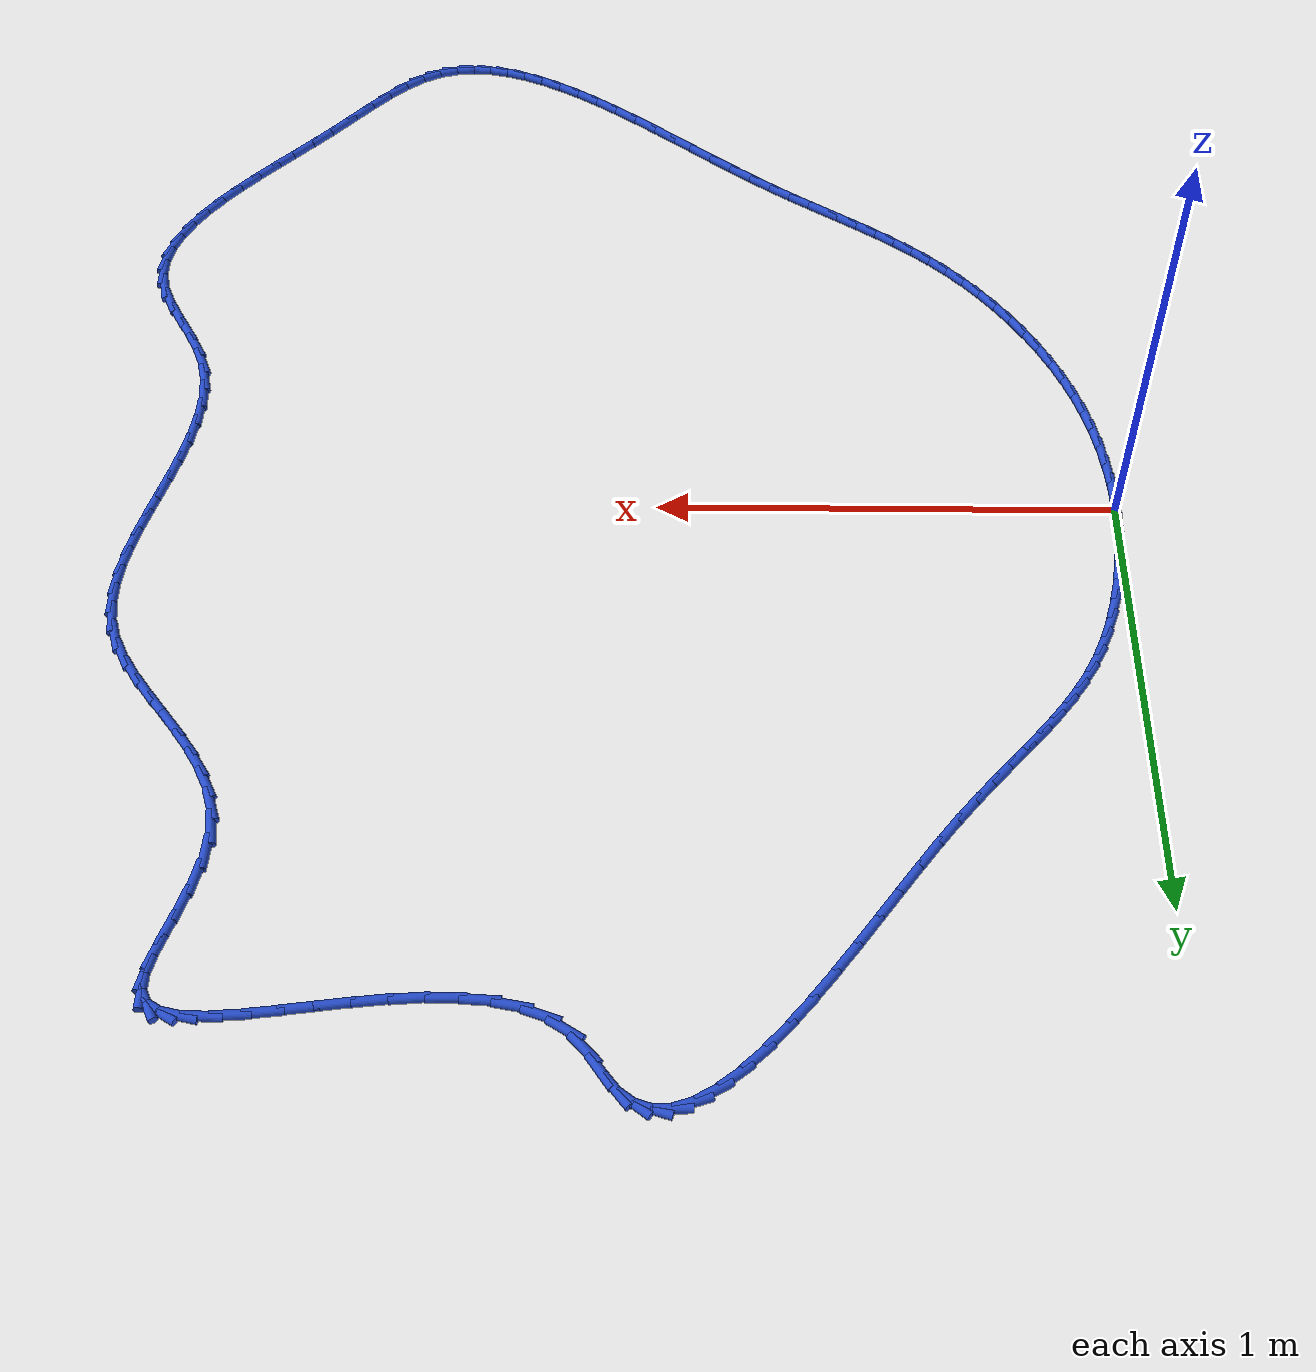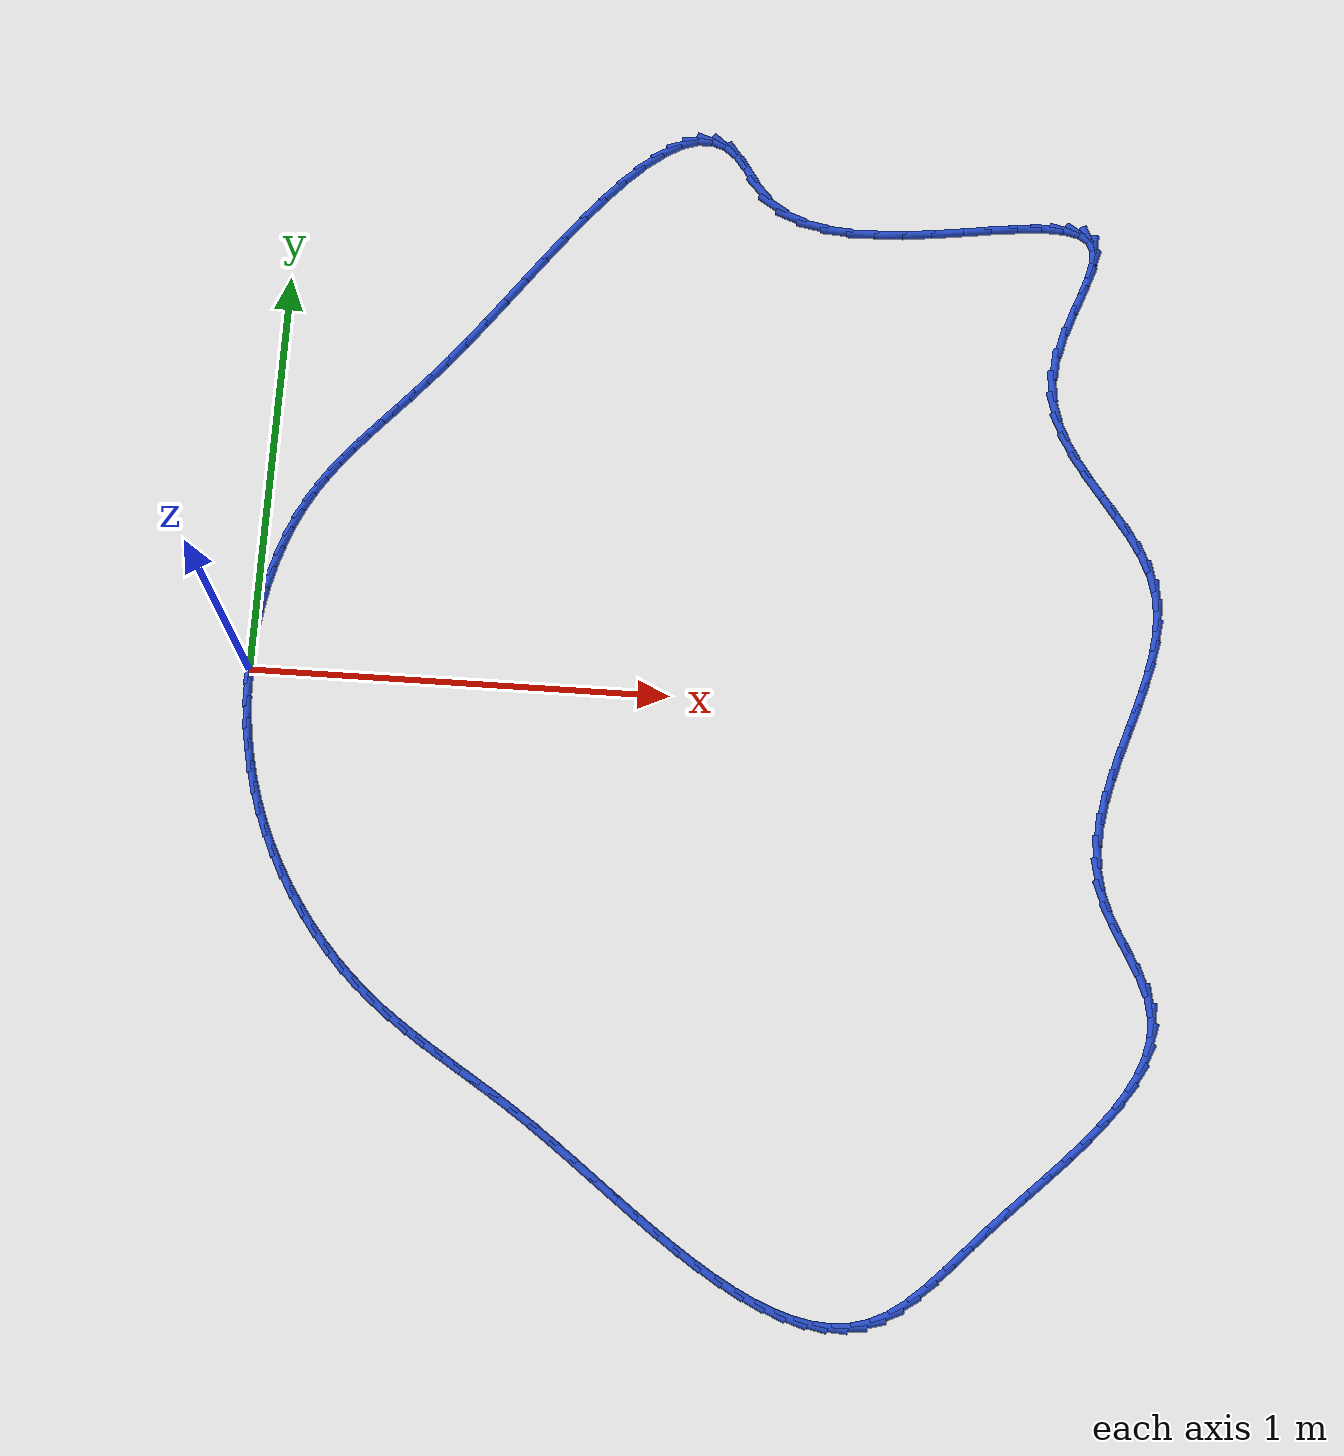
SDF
<sdf version="1.6">
 <world name="default">
  <light name="sun" type="directional">
   <pose>0 0 10 0 -0 0</pose>
   <diffuse>0.8 0.8 0.8 1</diffuse>
   <specular>0.2 0.2 0.2 1</specular>
   <attenuation>
    <range>1000</range>
    <constant>0.9</constant>
    <linear>0.01</linear>
    <quadratic>0.001</quadratic>
   </attenuation>
   <direction>-0.5 0.1 -0.9</direction>
  </light>
  <model name="ground_plane">
   <static>1</static>
   <link name="link">
    <collision name="collision">
     <geometry><plane><normal>0 0 1</normal><size>100 100</size></plane></geometry>
     <surface><friction><ode><mu>100</mu><mu2>50</mu2></ode></friction></surface>
    </collision>
    <visual name="visual">
     <cast_shadows>0</cast_shadows>
     <geometry><plane><normal>0 0 1</normal><size>100 100</size></plane></geometry>
     <material>
      <script><uri>file://media/materials/scripts/gazebo.material</uri><name>Gazebo/WhiteGlow</name></script>
     </material>
    </visual>
   </link>
  </model>
  <gravity>0 0 -9.8</gravity>
  <magnetic_field>6e-06 2.3e-05 -4.2e-05</magnetic_field>
  <atmosphere type="adiabatic"/>
  <physics name="default_physics" default="0" type="ode">
   <max_step_size>0.001</max_step_size>
   <real_time_factor>1</real_time_factor>
   <real_time_update_rate>1000</real_time_update_rate>
  </physics>
  <scene><ambient>0.4 0.4 0.4 1</ambient><background>0.7 0.7 0.7 1</background><shadows>1</shadows></scene>
  <spherical_coordinates>
   <surface_model>EARTH_WGS84</surface_model>
   <latitude_deg>0</latitude_deg>
   <longitude_deg>0</longitude_deg>
   <elevation>0</elevation>
   <heading_deg>0</heading_deg>
  </spherical_coordinates>
  <model name="line">
   <link name="link_0">
    <pose>2.949029909160572e-17 -4.163336342344337e-17 0.01 0 1.57 1.544740672575645</pose>
    <collision name="collision">
     <geometry><cylinder><radius>0.01</radius><length>0.08</length></cylinder></geometry>
    </collision>
    <visual name="visual">
     <material>
      <script><name>Gazebo/Blue</name><uri>file://media/materials/scripts/gazebo.material</uri></script>
     </material>
     <geometry><cylinder><radius>0.01</radius><length>0.08</length></cylinder></geometry>
    </visual>
   </link>
   <link name="link_1">
    <pose>0.0014229188802898308 0.05459839344539533 0.01 0 1.57 1.4936639560395963</pose>
    <collision name="collision">
     <geometry><cylinder><radius>0.01</radius><length>0.08</length></cylinder></geometry>
    </collision>
    <visual name="visual">
     <material>
      <script><name>Gazebo/Blue</name><uri>file://media/materials/scripts/gazebo.material</uri></script>
     </material>
     <geometry><cylinder><radius>0.01</radius><length>0.08</length></cylinder></geometry>
    </visual>
   </link>
   <link name="link_2">
    <pose>0.005649222591563145 0.1092825554434124 0.01 0 1.57 1.4421383450726681</pose>
    <collision name="collision">
     <geometry><cylinder><radius>0.01</radius><length>0.08</length></cylinder></geometry>
    </collision>
    <visual name="visual">
     <material>
      <script><name>Gazebo/Blue</name><uri>file://media/materials/scripts/gazebo.material</uri></script>
     </material>
     <geometry><cylinder><radius>0.01</radius><length>0.08</length></cylinder></geometry>
    </visual>
   </link>
   <link name="link_3">
    <pose>0.012674637058225538 0.16358628323030236 0.01 0 1.57 1.3891185103644323</pose>
    <collision name="collision">
     <geometry><cylinder><radius>0.01</radius><length>0.08</length></cylinder></geometry>
    </collision>
    <visual name="visual">
     <material>
      <script><name>Gazebo/Blue</name><uri>file://media/materials/scripts/gazebo.material</uri></script>
     </material>
     <geometry><cylinder><radius>0.01</radius><length>0.08</length></cylinder></geometry>
    </visual>
   </link>
   <link name="link_4">
    <pose>0.0224948882046826 0.2170433740423164 0.01 0 1.57 1.333507791245873</pose>
    <collision name="collision">
     <geometry><cylinder><radius>0.01</radius><length>0.08</length></cylinder></geometry>
    </collision>
    <visual name="visual">
     <material>
      <script><name>Gazebo/Blue</name><uri>file://media/materials/scripts/gazebo.material</uri></script>
     </material>
     <geometry><cylinder><radius>0.01</radius><length>0.08</length></cylinder></geometry>
    </visual>
   </link>
   <link name="link_5">
    <pose>0.03510570195533986 0.26918762511570565 0.01 0 1.57 1.274110096249701</pose>
    <collision name="collision">
     <geometry><cylinder><radius>0.01</radius><length>0.08</length></cylinder></geometry>
    </collision>
    <visual name="visual">
     <material>
      <script><name>Gazebo/Blue</name><uri>file://media/materials/scripts/gazebo.material</uri></script>
     </material>
     <geometry><cylinder><radius>0.01</radius><length>0.08</length></cylinder></geometry>
    </visual>
   </link>
   <link name="link_6">
    <pose>0.05050280423460295 0.31955283368672155 0.01 0 1.57 1.2095841343453633</pose>
    <collision name="collision">
     <geometry><cylinder><radius>0.01</radius><length>0.08</length></cylinder></geometry>
    </collision>
    <visual name="visual">
     <material>
      <script><name>Gazebo/Blue</name><uri>file://media/materials/scripts/gazebo.material</uri></script>
     </material>
     <geometry><cylinder><radius>0.01</radius><length>0.08</length></cylinder></geometry>
    </visual>
   </link>
   <link name="link_7">
    <pose>0.06868192096687742 0.36767279699161515 0.01 0 1.57 1.1384117896232102</pose>
    <collision name="collision">
     <geometry><cylinder><radius>0.01</radius><length>0.08</length></cylinder></geometry>
    </collision>
    <visual name="visual">
     <material>
      <script><name>Gazebo/Blue</name><uri>file://media/materials/scripts/gazebo.material</uri></script>
     </material>
     <geometry><cylinder><radius>0.01</radius><length>0.08</length></cylinder></geometry>
    </visual>
   </link>
   <link name="link_8">
    <pose>0.08963869787432686 0.4130819203028877 0.01 0 1.57 1.062642803439044</pose>
    <collision name="collision">
     <geometry><cylinder><radius>0.01</radius><length>0.08</length></cylinder></geometry>
    </collision>
    <visual name="visual">
     <material>
      <script><name>Gazebo/Blue</name><uri>file://media/materials/scripts/gazebo.material</uri></script>
     </material>
     <geometry><cylinder><radius>0.01</radius><length>0.08</length></cylinder></geometry>
    </visual>
   </link>
   <link name="link_9">
    <pose>0.11332873403195523 0.4556182140362352 0.01 0 1.57 0.9929972902564257</pose>
    <collision name="collision">
     <geometry><cylinder><radius>0.01</radius><length>0.08</length></cylinder></geometry>
    </collision>
    <visual name="visual">
     <material>
      <script><name>Gazebo/Blue</name><uri>file://media/materials/scripts/gazebo.material</uri></script>
     </material>
     <geometry><cylinder><radius>0.01</radius><length>0.08</length></cylinder></geometry>
    </visual>
   </link>
   <link name="link_10">
    <pose>0.13960282709685687 0.49591421828082727 0.01 0 1.57 0.9342637249670979</pose>
    <collision name="collision">
     <geometry><cylinder><radius>0.01</radius><length>0.08</length></cylinder></geometry>
    </collision>
    <visual name="visual">
     <material>
      <script><name>Gazebo/Blue</name><uri>file://media/materials/scripts/gazebo.material</uri></script>
     </material>
     <geometry><cylinder><radius>0.01</radius><length>0.08</length></cylinder></geometry>
    </visual>
   </link>
   <link name="link_11">
    <pose>0.168294841850847 0.5347308461205417 0.01 0 1.57 0.8886530395660981</pose>
    <collision name="collision">
     <geometry><cylinder><radius>0.01</radius><length>0.08</length></cylinder></geometry>
    </collision>
    <visual name="visual">
     <material>
      <script><name>Gazebo/Blue</name><uri>file://media/materials/scripts/gazebo.material</uri></script>
     </material>
     <geometry><cylinder><radius>0.01</radius><length>0.08</length></cylinder></geometry>
    </visual>
   </link>
   <link name="link_12">
    <pose>0.19923864307574055 0.5728290106392558 0.01 0 1.57 0.8570912512732618</pose>
    <collision name="collision">
     <geometry><cylinder><radius>0.01</radius><length>0.08</length></cylinder></geometry>
    </collision>
    <visual name="visual">
     <material>
      <script><name>Gazebo/Blue</name><uri>file://media/materials/scripts/gazebo.material</uri></script>
     </material>
     <geometry><cylinder><radius>0.01</radius><length>0.08</length></cylinder></geometry>
    </visual>
   </link>
   <link name="link_13">
    <pose>0.23226809555335265 0.610969624920847 0.01 0 1.57 0.8394103957964334</pose>
    <collision name="collision">
     <geometry><cylinder><radius>0.01</radius><length>0.08</length></cylinder></geometry>
    </collision>
    <visual name="visual">
     <material>
      <script><name>Gazebo/Blue</name><uri>file://media/materials/scripts/gazebo.material</uri></script>
     </material>
     <geometry><cylinder><radius>0.01</radius><length>0.08</length></cylinder></geometry>
    </visual>
   </link>
   <link name="link_14">
    <pose>0.2672170640654984 0.6499136020491925 0.01 0 1.57 0.8346508001226272</pose>
    <collision name="collision">
     <geometry><cylinder><radius>0.01</radius><length>0.08</length></cylinder></geometry>
    </collision>
    <visual name="visual">
     <material>
      <script><name>Gazebo/Blue</name><uri>file://media/materials/scripts/gazebo.material</uri></script>
     </material>
     <geometry><cylinder><radius>0.01</radius><length>0.08</length></cylinder></geometry>
    </visual>
   </link>
   <link name="link_15">
    <pose>0.3039194133939929 0.6904218551081704 0.01 0 1.57 0.8413514955589014</pose>
    <collision name="collision">
     <geometry><cylinder><radius>0.01</radius><length>0.08</length></cylinder></geometry>
    </collision>
    <visual name="visual">
     <material>
      <script><name>Gazebo/Blue</name><uri>file://media/materials/scripts/gazebo.material</uri></script>
     </material>
     <geometry><cylinder><radius>0.01</radius><length>0.08</length></cylinder></geometry>
    </visual>
   </link>
   <link name="link_16">
    <pose>0.34220900832065115 0.7332552971816575 0.01 0 1.57 0.8577790385005601</pose>
    <collision name="collision">
     <geometry><cylinder><radius>0.01</radius><length>0.08</length></cylinder></geometry>
    </collision>
    <visual name="visual">
     <material>
      <script><name>Gazebo/Blue</name><uri>file://media/materials/scripts/gazebo.material</uri></script>
     </material>
     <geometry><cylinder><radius>0.01</radius><length>0.08</length></cylinder></geometry>
    </visual>
   </link>
   <link name="link_17">
    <pose>0.3819197136272883 0.7791748413535313 0.01 0 1.57 0.8820590638127545</pose>
    <collision name="collision">
     <geometry><cylinder><radius>0.01</radius><length>0.08</length></cylinder></geometry>
    </collision>
    <visual name="visual">
     <material>
      <script><name>Gazebo/Blue</name><uri>file://media/materials/scripts/gazebo.material</uri></script>
     </material>
     <geometry><cylinder><radius>0.01</radius><length>0.08</length></cylinder></geometry>
    </visual>
   </link>
   <link name="link_18">
    <pose>0.4228852840105257 0.8289377212351565 0.01 0 1.57 0.9073994049085606</pose>
    <collision name="collision">
     <geometry><cylinder><radius>0.01</radius><length>0.08</length></cylinder></geometry>
    </collision>
    <visual name="visual">
     <material>
      <script><name>Gazebo/Blue</name><uri>file://media/materials/scripts/gazebo.material</uri></script>
     </material>
     <geometry><cylinder><radius>0.01</radius><length>0.08</length></cylinder></geometry>
    </visual>
   </link>
   <link name="link_19">
    <pose>0.46492218971144633 0.8827234571510989 0.01 0 1.57 0.9239365346075642</pose>
    <collision name="collision">
     <geometry><cylinder><radius>0.01</radius><length>0.08</length></cylinder></geometry>
    </collision>
    <visual name="visual">
     <material>
      <script><name>Gazebo/Blue</name><uri>file://media/materials/scripts/gazebo.material</uri></script>
     </material>
     <geometry><cylinder><radius>0.01</radius><length>0.08</length></cylinder></geometry>
    </visual>
   </link>
   <link name="link_20">
    <pose>0.507810955171338 0.9395101219114486 0.01 0 1.57 0.932174153599378</pose>
    <collision name="collision">
     <geometry><cylinder><radius>0.01</radius><length>0.08</length></cylinder></geometry>
    </collision>
    <visual name="visual">
     <material>
      <script><name>Gazebo/Blue</name><uri>file://media/materials/scripts/gazebo.material</uri></script>
     </material>
     <geometry><cylinder><radius>0.01</radius><length>0.08</length></cylinder></geometry>
    </visual>
   </link>
   <link name="link_21">
    <pose>0.5513276226211673 0.9981259755392177 0.01 0 1.57 0.9330900064289085</pose>
    <collision name="collision">
     <geometry><cylinder><radius>0.01</radius><length>0.08</length></cylinder></geometry>
    </collision>
    <visual name="visual">
     <material>
      <script><name>Gazebo/Blue</name><uri>file://media/materials/scripts/gazebo.material</uri></script>
     </material>
     <geometry><cylinder><radius>0.01</radius><length>0.08</length></cylinder></geometry>
    </visual>
   </link>
   <link name="link_22">
    <pose>0.5952482342918994 1.057399278057417 0.01 0 1.57 0.9269539566968109</pose>
    <collision name="collision">
     <geometry><cylinder><radius>0.01</radius><length>0.08</length></cylinder></geometry>
    </collision>
    <visual name="visual">
     <material>
      <script><name>Gazebo/Blue</name><uri>file://media/materials/scripts/gazebo.material</uri></script>
     </material>
     <geometry><cylinder><radius>0.01</radius><length>0.08</length></cylinder></geometry>
    </visual>
   </link>
   <link name="link_23">
    <pose>0.6393488324145011 1.1161582894890594 0.01 0 1.57 0.9134040262255821</pose>
    <collision name="collision">
     <geometry><cylinder><radius>0.01</radius><length>0.08</length></cylinder></geometry>
    </collision>
    <visual name="visual">
     <material>
      <script><name>Gazebo/Blue</name><uri>file://media/materials/scripts/gazebo.material</uri></script>
     </material>
     <geometry><cylinder><radius>0.01</radius><length>0.08</length></cylinder></geometry>
    </visual>
   </link>
   <link name="link_24">
    <pose>0.6834054592199379 1.173231269857155 0.01 0 1.57 0.8913882123612406</pose>
    <collision name="collision">
     <geometry><cylinder><radius>0.01</radius><length>0.08</length></cylinder></geometry>
    </collision>
    <visual name="visual">
     <material>
      <script><name>Gazebo/Blue</name><uri>file://media/materials/scripts/gazebo.material</uri></script>
     </material>
     <geometry><cylinder><radius>0.01</radius><length>0.08</length></cylinder></geometry>
    </visual>
   </link>
   <link name="link_25">
    <pose>0.7271941569391759 1.2274464791847166 0.01 0 1.57 0.8589569287098184</pose>
    <collision name="collision">
     <geometry><cylinder><radius>0.01</radius><length>0.08</length></cylinder></geometry>
    </collision>
    <visual name="visual">
     <material>
      <script><name>Gazebo/Blue</name><uri>file://media/materials/scripts/gazebo.material</uri></script>
     </material>
     <geometry><cylinder><radius>0.01</radius><length>0.08</length></cylinder></geometry>
    </visual>
   </link>
   <link name="link_26">
    <pose>0.7704909678031808 1.2776321774947546 0.01 0 1.57 0.8128391091976263</pose>
    <collision name="collision">
     <geometry><cylinder><radius>0.01</radius><length>0.08</length></cylinder></geometry>
    </collision>
    <visual name="visual">
     <material>
      <script><name>Gazebo/Blue</name><uri>file://media/materials/scripts/gazebo.material</uri></script>
     </material>
     <geometry><cylinder><radius>0.01</radius><length>0.08</length></cylinder></geometry>
    </visual>
   </link>
   <link name="link_27">
    <pose>0.8130719340429191 1.3226166248102815 0.01 0 1.57 0.7476639512551123</pose>
    <collision name="collision">
     <geometry><cylinder><radius>0.01</radius><length>0.08</length></cylinder></geometry>
    </collision>
    <visual name="visual">
     <material>
      <script><name>Gazebo/Blue</name><uri>file://media/materials/scripts/gazebo.material</uri></script>
     </material>
     <geometry><cylinder><radius>0.01</radius><length>0.08</length></cylinder></geometry>
    </visual>
   </link>
   <link name="link_28">
    <pose>0.8547130978893562 1.3612280811543085 0.01 0 1.57 0.6546123008137925</pose>
    <collision name="collision">
     <geometry><cylinder><radius>0.01</radius><length>0.08</length></cylinder></geometry>
    </collision>
    <visual name="visual">
     <material>
      <script><name>Gazebo/Blue</name><uri>file://media/materials/scripts/gazebo.material</uri></script>
     </material>
     <geometry><cylinder><radius>0.01</radius><length>0.08</length></cylinder></geometry>
    </visual>
   </link>
   <link name="link_29">
    <pose>0.8951905015734587 1.3922948065498473 0.01 0 1.57 0.5194023976951444</pose>
    <collision name="collision">
     <geometry><cylinder><radius>0.01</radius><length>0.08</length></cylinder></geometry>
    </collision>
    <visual name="visual">
     <material>
      <script><name>Gazebo/Blue</name><uri>file://media/materials/scripts/gazebo.material</uri></script>
     </material>
     <geometry><cylinder><radius>0.01</radius><length>0.08</length></cylinder></geometry>
    </visual>
   </link>
   <link name="link_30">
    <pose>0.9342801873261919 1.4146450610199093 0.01 0 1.57 0.3210149081090921</pose>
    <collision name="collision">
     <geometry><cylinder><radius>0.01</radius><length>0.08</length></cylinder></geometry>
    </collision>
    <visual name="visual">
     <material>
      <script><name>Gazebo/Blue</name><uri>file://media/materials/scripts/gazebo.material</uri></script>
     </material>
     <geometry><cylinder><radius>0.01</radius><length>0.08</length></cylinder></geometry>
    </visual>
   </link>
   <link name="link_31">
    <pose>0.9717581973785224 1.4271071045875063 0.01 0 1.57 0.03931752774718461</pose>
    <collision name="collision">
     <geometry><cylinder><radius>0.01</radius><length>0.08</length></cylinder></geometry>
    </collision>
    <visual name="visual">
     <material>
      <script><name>Gazebo/Blue</name><uri>file://media/materials/scripts/gazebo.material</uri></script>
     </material>
     <geometry><cylinder><radius>0.01</radius><length>0.08</length></cylinder></geometry>
    </visual>
   </link>
   <link name="link_32">
    <pose>1.0074005739614154 1.4285091972756494 0.01 0 1.57 -0.3119461464083098</pose>
    <collision name="collision">
     <geometry><cylinder><radius>0.01</radius><length>0.08</length></cylinder></geometry>
    </collision>
    <visual name="visual">
     <material>
      <script><name>Gazebo/Blue</name><uri>file://media/materials/scripts/gazebo.material</uri></script>
     </material>
     <geometry><cylinder><radius>0.01</radius><length>0.08</length></cylinder></geometry>
    </visual>
   </link>
   <link name="link_33">
    <pose>1.0409833593058377 1.4176795991073508 0.01 0 1.57 -0.6588332465115055</pose>
    <collision name="collision">
     <geometry><cylinder><radius>0.01</radius><length>0.08</length></cylinder></geometry>
    </collision>
    <visual name="visual">
     <material>
      <script><name>Gazebo/Blue</name><uri>file://media/materials/scripts/gazebo.material</uri></script>
     </material>
     <geometry><cylinder><radius>0.01</radius><length>0.08</length></cylinder></geometry>
    </visual>
   </link>
   <link name="link_34">
    <pose>1.0722825956427549 1.3934465701056216 0.01 0 1.57 -0.9186454093857453</pose>
    <collision name="collision">
     <geometry><cylinder><radius>0.01</radius><length>0.08</length></cylinder></geometry>
    </collision>
    <visual name="visual">
     <material>
      <script><name>Gazebo/Blue</name><uri>file://media/materials/scripts/gazebo.material</uri></script>
     </material>
     <geometry><cylinder><radius>0.01</radius><length>0.08</length></cylinder></geometry>
    </visual>
   </link>
   <link name="link_35">
    <pose>1.1013827500937137 1.3553376058404263 0.01 0 1.57 -0.9775569772916918</pose>
    <collision name="collision">
     <geometry><cylinder><radius>0.01</radius><length>0.08</length></cylinder></geometry>
    </collision>
    <visual name="visual">
     <material>
      <script><name>Gazebo/Blue</name><uri>file://media/materials/scripts/gazebo.material</uri></script>
     </material>
     <geometry><cylinder><radius>0.01</radius><length>0.08</length></cylinder></geometry>
    </visual>
   </link>
   <link name="link_36">
    <pose>1.131684031639837 1.3103973791379775 0.01 0 1.57 -0.829667757174458</pose>
    <collision name="collision">
     <geometry><cylinder><radius>0.01</radius><length>0.08</length></cylinder></geometry>
    </collision>
    <visual name="visual">
     <material>
      <script><name>Gazebo/Blue</name><uri>file://media/materials/scripts/gazebo.material</uri></script>
     </material>
     <geometry><cylinder><radius>0.01</radius><length>0.08</length></cylinder></geometry>
    </visual>
   </link>
   <link name="link_37">
    <pose>1.1685401842341017 1.2701245244155892 0.01 0 1.57 -0.567876123459904</pose>
    <collision name="collision">
     <geometry><cylinder><radius>0.01</radius><length>0.08</length></cylinder></geometry>
    </collision>
    <visual name="visual">
     <material>
      <script><name>Gazebo/Blue</name><uri>file://media/materials/scripts/gazebo.material</uri></script>
     </material>
     <geometry><cylinder><radius>0.01</radius><length>0.08</length></cylinder></geometry>
    </visual>
   </link>
   <link name="link_38">
    <pose>1.2145151508487457 1.2407935913253583 0.01 0 1.57 -0.3454019647571306</pose>
    <collision name="collision">
     <geometry><cylinder><radius>0.01</radius><length>0.08</length></cylinder></geometry>
    </collision>
    <visual name="visual">
     <material>
      <script><name>Gazebo/Blue</name><uri>file://media/materials/scripts/gazebo.material</uri></script>
     </material>
     <geometry><cylinder><radius>0.01</radius><length>0.08</length></cylinder></geometry>
    </visual>
   </link>
   <link name="link_39">
    <pose>1.2683129445316885 1.2214357203151238 0.01 0 1.57 -0.17920527930912616</pose>
    <collision name="collision">
     <geometry><cylinder><radius>0.01</radius><length>0.08</length></cylinder></geometry>
    </collision>
    <visual name="visual">
     <material>
      <script><name>Gazebo/Blue</name><uri>file://media/materials/scripts/gazebo.material</uri></script>
     </material>
     <geometry><cylinder><radius>0.01</radius><length>0.08</length></cylinder></geometry>
    </visual>
   </link>
   <link name="link_40">
    <pose>1.3283586011334718 1.2105585330023614 0.01 0 1.57 -0.060016969714293315</pose>
    <collision name="collision">
     <geometry><cylinder><radius>0.01</radius><length>0.08</length></cylinder></geometry>
    </collision>
    <visual name="visual">
     <material>
      <script><name>Gazebo/Blue</name><uri>file://media/materials/scripts/gazebo.material</uri></script>
     </material>
     <geometry><cylinder><radius>0.01</radius><length>0.08</length></cylinder></geometry>
    </visual>
   </link>
   <link name="link_41">
    <pose>1.3930771565046371 1.2066696510045476 0.01 0 1.57 0.02369253003492182</pose>
    <collision name="collision">
     <geometry><cylinder><radius>0.01</radius><length>0.08</length></cylinder></geometry>
    </collision>
    <visual name="visual">
     <material>
      <script><name>Gazebo/Blue</name><uri>file://media/materials/scripts/gazebo.material</uri></script>
     </material>
     <geometry><cylinder><radius>0.01</radius><length>0.08</length></cylinder></geometry>
    </visual>
   </link>
   <link name="link_42">
    <pose>1.4608936464957256 1.2082766959391587 0.01 0 1.57 0.08073897221709905</pose>
    <collision name="collision">
     <geometry><cylinder><radius>0.01</radius><length>0.08</length></cylinder></geometry>
    </collision>
    <visual name="visual">
     <material>
      <script><name>Gazebo/Blue</name><uri>file://media/materials/scripts/gazebo.material</uri></script>
     </material>
     <geometry><cylinder><radius>0.01</radius><length>0.08</length></cylinder></geometry>
    </visual>
   </link>
   <link name="link_43">
    <pose>1.5302331069572785 1.2138872894236694 0.01 0 1.57 0.11668588335635247</pose>
    <collision name="collision">
     <geometry><cylinder><radius>0.01</radius><length>0.08</length></cylinder></geometry>
    </collision>
    <visual name="visual">
     <material>
      <script><name>Gazebo/Blue</name><uri>file://media/materials/scripts/gazebo.material</uri></script>
     </material>
     <geometry><cylinder><radius>0.01</radius><length>0.08</length></cylinder></geometry>
    </visual>
   </link>
   <link name="link_44">
    <pose>1.5995205737398386 1.2220090530755574 0.01 0 1.57 0.13428143098976908</pose>
    <collision name="collision">
     <geometry><cylinder><radius>0.01</radius><length>0.08</length></cylinder></geometry>
    </collision>
    <visual name="visual">
     <material>
      <script><name>Gazebo/Blue</name><uri>file://media/materials/scripts/gazebo.material</uri></script>
     </material>
     <geometry><cylinder><radius>0.01</radius><length>0.08</length></cylinder></geometry>
    </visual>
   </link>
   <link name="link_45">
    <pose>1.6671810826939468 1.231149608512298 0.01 0 1.57 0.13365633224945683</pose>
    <collision name="collision">
     <geometry><cylinder><radius>0.01</radius><length>0.08</length></cylinder></geometry>
    </collision>
    <visual name="visual">
     <material>
      <script><name>Gazebo/Blue</name><uri>file://media/materials/scripts/gazebo.material</uri></script>
     </material>
     <geometry><cylinder><radius>0.01</radius><length>0.08</length></cylinder></geometry>
    </visual>
   </link>
   <link name="link_46">
    <pose>1.7316396696701437 1.2398165773513674 0.01 0 1.57 0.11181075503974047</pose>
    <collision name="collision">
     <geometry><cylinder><radius>0.01</radius><length>0.08</length></cylinder></geometry>
    </collision>
    <visual name="visual">
     <material>
      <script><name>Gazebo/Blue</name><uri>file://media/materials/scripts/gazebo.material</uri></script>
     </material>
     <geometry><cylinder><radius>0.01</radius><length>0.08</length></cylinder></geometry>
    </visual>
   </link>
   <link name="link_47">
    <pose>1.791321370518972 1.2465175812102418 0.01 0 1.57 0.060729087863976246</pose>
    <collision name="collision">
     <geometry><cylinder><radius>0.01</radius><length>0.08</length></cylinder></geometry>
    </collision>
    <visual name="visual">
     <material>
      <script><name>Gazebo/Blue</name><uri>file://media/materials/scripts/gazebo.material</uri></script>
     </material>
     <geometry><cylinder><radius>0.01</radius><length>0.08</length></cylinder></geometry>
    </visual>
   </link>
   <link name="link_48">
    <pose>1.844651221090973 1.2497602417063967 0.01 0 1.57 -0.03760224628985859</pose>
    <collision name="collision">
     <geometry><cylinder><radius>0.01</radius><length>0.08</length></cylinder></geometry>
    </collision>
    <visual name="visual">
     <material>
      <script><name>Gazebo/Blue</name><uri>file://media/materials/scripts/gazebo.material</uri></script>
     </material>
     <geometry><cylinder><radius>0.01</radius><length>0.08</length></cylinder></geometry>
    </visual>
   </link>
   <link name="link_49">
    <pose>1.8900542572366872 1.2480521804573088 0.01 0 1.57 -0.22325899801947988</pose>
    <collision name="collision">
     <geometry><cylinder><radius>0.01</radius><length>0.08</length></cylinder></geometry>
    </collision>
    <visual name="visual">
     <material>
      <script><name>Gazebo/Blue</name><uri>file://media/materials/scripts/gazebo.material</uri></script>
     </material>
     <geometry><cylinder><radius>0.01</radius><length>0.08</length></cylinder></geometry>
    </visual>
   </link>
   <link name="link_50">
    <pose>1.9259555148066578 1.239901019080454 0.01 0 1.57 -0.5749780105822772</pose>
    <collision name="collision">
     <geometry><cylinder><radius>0.01</radius><length>0.08</length></cylinder></geometry>
    </collision>
    <visual name="visual">
     <material>
      <script><name>Gazebo/Blue</name><uri>file://media/materials/scripts/gazebo.material</uri></script>
     </material>
     <geometry><cylinder><radius>0.01</radius><length>0.08</length></cylinder></geometry>
    </visual>
   </link>
   <link name="link_51">
    <pose>1.9507800296514257 1.223814379193309 0.01 0 1.57 -1.125641032401646</pose>
    <collision name="collision">
     <geometry><cylinder><radius>0.01</radius><length>0.08</length></cylinder></geometry>
    </collision>
    <visual name="visual">
     <material>
      <script><name>Gazebo/Blue</name><uri>file://media/materials/scripts/gazebo.material</uri></script>
     </material>
     <geometry><cylinder><radius>0.01</radius><length>0.08</length></cylinder></geometry>
    </visual>
   </link>
   <link name="link_52">
    <pose>1.9629528376215326 1.1982998824133486 0.01 0 1.57 1.5390060604563676</pose>
    <collision name="collision">
     <geometry><cylinder><radius>0.01</radius><length>0.08</length></cylinder></geometry>
    </collision>
    <visual name="visual">
     <material>
      <script><name>Gazebo/Blue</name><uri>file://media/materials/scripts/gazebo.material</uri></script>
     </material>
     <geometry><cylinder><radius>0.01</radius><length>0.08</length></cylinder></geometry>
    </visual>
   </link>
   <link name="link_53">
    <pose>1.961813433507063 1.1624706684891108 0.01 0 1.57 1.3194422107451074</pose>
    <collision name="collision">
     <geometry><cylinder><radius>0.01</radius><length>0.08</length></cylinder></geometry>
    </collision>
    <visual name="visual">
     <material>
      <script><name>Gazebo/Blue</name><uri>file://media/materials/scripts/gazebo.material</uri></script>
     </material>
     <geometry><cylinder><radius>0.01</radius><length>0.08</length></cylinder></geometry>
    </visual>
   </link>
   <link name="link_54">
    <pose>1.9503584774840803 1.1178615057997219 0.01 0 1.57 1.235468332689689</pose>
    <collision name="collision">
     <geometry><cylinder><radius>0.01</radius><length>0.08</length></cylinder></geometry>
    </collision>
    <visual name="visual">
     <material>
      <script><name>Gazebo/Blue</name><uri>file://media/materials/scripts/gazebo.material</uri></script>
     </material>
     <geometry><cylinder><radius>0.01</radius><length>0.08</length></cylinder></geometry>
    </visual>
   </link>
   <link name="link_55">
    <pose>1.932498753512809 1.0666124589288823 0.01 0 1.57 1.220736446601239</pose>
    <collision name="collision">
     <geometry><cylinder><radius>0.01</radius><length>0.08</length></cylinder></geometry>
    </collision>
    <visual name="visual">
     <material>
      <script><name>Gazebo/Blue</name><uri>file://media/materials/scripts/gazebo.material</uri></script>
     </material>
     <geometry><cylinder><radius>0.01</radius><length>0.08</length></cylinder></geometry>
    </visual>
   </link>
   <link name="link_56">
    <pose>1.9121450455534723 1.010863592460291 0.01 0 1.57 1.2557613855150864</pose>
    <collision name="collision">
     <geometry><cylinder><radius>0.01</radius><length>0.08</length></cylinder></geometry>
    </collision>
    <visual name="visual">
     <material>
      <script><name>Gazebo/Blue</name><uri>file://media/materials/scripts/gazebo.material</uri></script>
     </material>
     <geometry><cylinder><radius>0.01</radius><length>0.08</length></cylinder></geometry>
    </visual>
   </link>
   <link name="link_57">
    <pose>1.8932081375662952 0.9527549709776483 0.01 0 1.57 1.3415743992632596</pose>
    <collision name="collision">
     <geometry><cylinder><radius>0.01</radius><length>0.08</length></cylinder></geometry>
    </collision>
    <visual name="visual">
     <material>
      <script><name>Gazebo/Blue</name><uri>file://media/materials/scripts/gazebo.material</uri></script>
     </material>
     <geometry><cylinder><radius>0.01</radius><length>0.08</length></cylinder></geometry>
    </visual>
   </link>
   <link name="link_58">
    <pose>1.8795988135114996 0.8944266590646522 0.01 0 1.57 1.4928756955531615</pose>
    <collision name="collision">
     <geometry><cylinder><radius>0.01</radius><length>0.08</length></cylinder></geometry>
    </collision>
    <visual name="visual">
     <material>
      <script><name>Gazebo/Blue</name><uri>file://media/materials/scripts/gazebo.material</uri></script>
     </material>
     <geometry><cylinder><radius>0.01</radius><length>0.08</length></cylinder></geometry>
    </visual>
   </link>
   <link name="link_59">
    <pose>1.8751933458520915 0.8380032463854884 0.01 0 1.57 -1.4489586201735758</pose>
    <collision name="collision">
     <geometry><cylinder><radius>0.01</radius><length>0.08</length></cylinder></geometry>
    </collision>
    <visual name="visual">
     <material>
      <script><name>Gazebo/Blue</name><uri>file://media/materials/scripts/gazebo.material</uri></script>
     </material>
     <geometry><cylinder><radius>0.01</radius><length>0.08</length></cylinder></geometry>
    </visual>
   </link>
   <link name="link_60">
    <pose>1.8817262665772074 0.7846489683998756 0.01 0 1.57 -1.2674911674700855</pose>
    <collision name="collision">
     <geometry><cylinder><radius>0.01</radius><length>0.08</length></cylinder></geometry>
    </collision>
    <visual name="visual">
     <material>
      <script><name>Gazebo/Blue</name><uri>file://media/materials/scripts/gazebo.material</uri></script>
     </material>
     <geometry><cylinder><radius>0.01</radius><length>0.08</length></cylinder></geometry>
    </visual>
   </link>
   <link name="link_61">
    <pose>1.8975708982278172 0.7340208977413101 0.01 0 1.57 -1.1230271457881533</pose>
    <collision name="collision">
     <geometry><cylinder><radius>0.01</radius><length>0.08</length></cylinder></geometry>
    </collision>
    <visual name="visual">
     <material>
      <script><name>Gazebo/Blue</name><uri>file://media/materials/scripts/gazebo.material</uri></script>
     </material>
     <geometry><cylinder><radius>0.01</radius><length>0.08</length></cylinder></geometry>
    </visual>
   </link>
   <link name="link_62">
    <pose>1.9208065202573374 0.6856442584281683 0.01 0 1.57 -1.0186904208480327</pose>
    <collision name="collision">
     <geometry><cylinder><radius>0.01</radius><length>0.08</length></cylinder></geometry>
    </collision>
    <visual name="visual">
     <material>
      <script><name>Gazebo/Blue</name><uri>file://media/materials/scripts/gazebo.material</uri></script>
     </material>
     <geometry><cylinder><radius>0.01</radius><length>0.08</length></cylinder></geometry>
    </visual>
   </link>
   <link name="link_63">
    <pose>1.9495124121191878 0.6390442744788283 0.01 0 1.57 -0.9520152506197481</pose>
    <collision name="collision">
     <geometry><cylinder><radius>0.01</radius><length>0.08</length></cylinder></geometry>
    </collision>
    <visual name="visual">
     <material>
      <script><name>Gazebo/Blue</name><uri>file://media/materials/scripts/gazebo.material</uri></script>
     </material>
     <geometry><cylinder><radius>0.01</radius><length>0.08</length></cylinder></geometry>
    </visual>
   </link>
   <link name="link_64">
    <pose>1.981767853266784 0.5937461699116662 0.01 0 1.57 -0.9196968085622255</pose>
    <collision name="collision">
     <geometry><cylinder><radius>0.01</radius><length>0.08</length></cylinder></geometry>
    </collision>
    <visual name="visual">
     <material>
      <script><name>Gazebo/Blue</name><uri>file://media/materials/scripts/gazebo.material</uri></script>
     </material>
     <geometry><cylinder><radius>0.01</radius><length>0.08</length></cylinder></geometry>
    </visual>
   </link>
   <link name="link_65">
    <pose>2.0156521231535445 0.5492751687450594 0.01 0 1.57 -0.920033027223478</pose>
    <collision name="collision">
     <geometry><cylinder><radius>0.01</radius><length>0.08</length></cylinder></geometry>
    </collision>
    <visual name="visual">
     <material>
      <script><name>Gazebo/Blue</name><uri>file://media/materials/scripts/gazebo.material</uri></script>
     </material>
     <geometry><cylinder><radius>0.01</radius><length>0.08</length></cylinder></geometry>
    </visual>
   </link>
   <link name="link_66">
    <pose>2.049244501232888 0.505156494997385 0.01 0 1.57 -0.9538629358773237</pose>
    <collision name="collision">
     <geometry><cylinder><radius>0.01</radius><length>0.08</length></cylinder></geometry>
    </collision>
    <visual name="visual">
     <material>
      <script><name>Gazebo/Blue</name><uri>file://media/materials/scripts/gazebo.material</uri></script>
     </material>
     <geometry><cylinder><radius>0.01</radius><length>0.08</length></cylinder></geometry>
    </visual>
   </link>
   <link name="link_67">
    <pose>2.0806242669582318 0.46091537268701943 0.01 0 1.57 -1.0247641055361782</pose>
    <collision name="collision">
     <geometry><cylinder><radius>0.01</radius><length>0.08</length></cylinder></geometry>
    </collision>
    <visual name="visual">
     <material>
      <script><name>Gazebo/Blue</name><uri>file://media/materials/scripts/gazebo.material</uri></script>
     </material>
     <geometry><cylinder><radius>0.01</radius><length>0.08</length></cylinder></geometry>
    </visual>
   </link>
   <link name="link_68">
    <pose>2.107870699782993 0.41607702583234035 0.01 0 1.57 -1.1383348934530855</pose>
    <collision name="collision">
     <geometry><cylinder><radius>0.01</radius><length>0.08</length></cylinder></geometry>
    </collision>
    <visual name="visual">
     <material>
      <script><name>Gazebo/Blue</name><uri>file://media/materials/scripts/gazebo.material</uri></script>
     </material>
     <geometry><cylinder><radius>0.01</radius><length>0.08</length></cylinder></geometry>
    </visual>
   </link>
   <link name="link_69">
    <pose>2.129063079160589 0.3701666784517245 0.01 0 1.57 -1.2967825729696023</pose>
    <collision name="collision">
     <geometry><cylinder><radius>0.01</radius><length>0.08</length></cylinder></geometry>
    </collision>
    <visual name="visual">
     <material>
      <script><name>Gazebo/Blue</name><uri>file://media/materials/scripts/gazebo.material</uri></script>
     </material>
     <geometry><cylinder><radius>0.01</radius><length>0.08</length></cylinder></geometry>
    </visual>
   </link>
   <link name="link_70">
    <pose>2.142395495577533 0.3227345613662644 0.01 0 1.57 -1.4619286982267723</pose>
    <collision name="collision">
     <geometry><cylinder><radius>0.01</radius><length>0.08</length></cylinder></geometry>
    </collision>
    <visual name="visual">
     <material>
      <script><name>Gazebo/Blue</name><uri>file://media/materials/scripts/gazebo.material</uri></script>
     </material>
     <geometry><cylinder><radius>0.01</radius><length>0.08</length></cylinder></geometry>
    </visual>
   </link>
   <link name="link_71">
    <pose>2.147755001122821 0.2736996465855709 0.01 0 1.57 1.5423381108671623</pose>
    <collision name="collision">
     <geometry><cylinder><radius>0.01</radius><length>0.08</length></cylinder></geometry>
    </collision>
    <visual name="visual">
     <material>
      <script><name>Gazebo/Blue</name><uri>file://media/materials/scripts/gazebo.material</uri></script>
     </material>
     <geometry><cylinder><radius>0.01</radius><length>0.08</length></cylinder></geometry>
    </visual>
   </link>
   <link name="link_72">
    <pose>2.14631924834913 0.22326200968839907 0.01 0 1.57 1.435649102913575</pose>
    <collision name="collision">
     <geometry><cylinder><radius>0.01</radius><length>0.08</length></cylinder></geometry>
    </collision>
    <visual name="visual">
     <material>
      <script><name>Gazebo/Blue</name><uri>file://media/materials/scripts/gazebo.material</uri></script>
     </material>
     <geometry><cylinder><radius>0.01</radius><length>0.08</length></cylinder></geometry>
    </visual>
   </link>
   <link name="link_73">
    <pose>2.139298366311125 0.17162879990710767 0.01 0 1.57 1.3575270055580089</pose>
    <collision name="collision">
     <geometry><cylinder><radius>0.01</radius><length>0.08</length></cylinder></geometry>
    </collision>
    <visual name="visual">
     <material>
      <script><name>Gazebo/Blue</name><uri>file://media/materials/scripts/gazebo.material</uri></script>
     </material>
     <geometry><cylinder><radius>0.01</radius><length>0.08</length></cylinder></geometry>
    </visual>
   </link>
   <link name="link_74">
    <pose>2.1279024840634735 0.11900716647405588 0.01 0 1.57 1.3046083486557793</pose>
    <collision name="collision">
     <geometry><cylinder><radius>0.01</radius><length>0.08</length></cylinder></geometry>
    </collision>
    <visual name="visual">
     <material>
      <script><name>Gazebo/Blue</name><uri>file://media/materials/scripts/gazebo.material</uri></script>
     </material>
     <geometry><cylinder><radius>0.01</radius><length>0.08</length></cylinder></geometry>
    </visual>
   </link>
   <link name="link_75">
    <pose>2.113341730660841 0.06560425862160273 0.01 0 1.57 1.273869089832275</pose>
    <collision name="collision">
     <geometry><cylinder><radius>0.01</radius><length>0.08</length></cylinder></geometry>
    </collision>
    <visual name="visual">
     <material>
      <script><name>Gazebo/Blue</name><uri>file://media/materials/scripts/gazebo.material</uri></script>
     </material>
     <geometry><cylinder><radius>0.01</radius><length>0.08</length></cylinder></geometry>
    </visual>
   </link>
   <link name="link_76">
    <pose>2.096826235157893 0.011627225582107145 0.01 0 1.57 1.2632644213254685</pose>
    <collision name="collision">
     <geometry><cylinder><radius>0.01</radius><length>0.08</length></cylinder></geometry>
    </collision>
    <visual name="visual">
     <material>
      <script><name>Gazebo/Blue</name><uri>file://media/materials/scripts/gazebo.material</uri></script>
     </material>
     <geometry><cylinder><radius>0.01</radius><length>0.08</length></cylinder></geometry>
    </visual>
   </link>
   <link name="link_77">
    <pose>2.079566126609295 -0.0427167834120716 0.01 0 1.57 1.2718921500244282</pose>
    <collision name="collision">
     <geometry><cylinder><radius>0.01</radius><length>0.08</length></cylinder></geometry>
    </collision>
    <visual name="visual">
     <material>
      <script><name>Gazebo/Blue</name><uri>file://media/materials/scripts/gazebo.material</uri></script>
     </material>
     <geometry><cylinder><radius>0.01</radius><length>0.08</length></cylinder></geometry>
    </visual>
   </link>
   <link name="link_78">
    <pose>2.062771534069714 -0.09722061912857322 0.01 0 1.57 1.299983507390627</pose>
    <collision name="collision">
     <geometry><cylinder><radius>0.01</radius><length>0.08</length></cylinder></geometry>
    </collision>
    <visual name="visual">
     <material>
      <script><name>Gazebo/Blue</name><uri>file://media/materials/scripts/gazebo.material</uri></script>
     </material>
     <geometry><cylinder><radius>0.01</radius><length>0.08</length></cylinder></geometry>
    </visual>
   </link>
   <link name="link_79">
    <pose>2.047652586593815 -0.15167713233504038 0.01 0 1.57 1.3488197064102432</pose>
    <collision name="collision">
     <geometry><cylinder><radius>0.01</radius><length>0.08</length></cylinder></geometry>
    </collision>
    <visual name="visual">
     <material>
      <script><name>Gazebo/Blue</name><uri>file://media/materials/scripts/gazebo.material</uri></script>
     </material>
     <geometry><cylinder><radius>0.01</radius><length>0.08</length></cylinder></geometry>
    </visual>
   </link>
   <link name="link_80">
    <pose>2.0354194132362644 -0.2058791737991122 0.01 0 1.57 1.4205198133109653</pose>
    <collision name="collision">
     <geometry><cylinder><radius>0.01</radius><length>0.08</length></cylinder></geometry>
    </collision>
    <visual name="visual">
     <material>
      <script><name>Gazebo/Blue</name><uri>file://media/materials/scripts/gazebo.material</uri></script>
     </material>
     <geometry><cylinder><radius>0.01</radius><length>0.08</length></cylinder></geometry>
    </visual>
   </link>
   <link name="link_81">
    <pose>2.0272821430517283 -0.2596195942884313 0.01 0 1.57 1.517499384583761</pose>
    <collision name="collision">
     <geometry><cylinder><radius>0.01</radius><length>0.08</length></cylinder></geometry>
    </collision>
    <visual name="visual">
     <material>
      <script><name>Gazebo/Blue</name><uri>file://media/materials/scripts/gazebo.material</uri></script>
     </material>
     <geometry><cylinder><radius>0.01</radius><length>0.08</length></cylinder></geometry>
    </visual>
   </link>
   <link name="link_82">
    <pose>2.0244509050948722 -0.31269124457063774 0.01 0 1.57 -1.5003150920802395</pose>
    <collision name="collision">
     <geometry><cylinder><radius>0.01</radius><length>0.08</length></cylinder></geometry>
    </collision>
    <visual name="visual">
     <material>
      <script><name>Gazebo/Blue</name><uri>file://media/materials/scripts/gazebo.material</uri></script>
     </material>
     <geometry><cylinder><radius>0.01</radius><length>0.08</length></cylinder></geometry>
    </visual>
   </link>
   <link name="link_83">
    <pose>2.0281358284203623 -0.3648869754133713 0.01 0 1.57 -1.3511423713404072</pose>
    <collision name="collision">
     <geometry><cylinder><radius>0.01</radius><length>0.08</length></cylinder></geometry>
    </collision>
    <visual name="visual">
     <material>
      <script><name>Gazebo/Blue</name><uri>file://media/materials/scripts/gazebo.material</uri></script>
     </material>
     <geometry><cylinder><radius>0.01</radius><length>0.08</length></cylinder></geometry>
    </visual>
   </link>
   <link name="link_84">
    <pose>2.0395470420828645 -0.41599963758427483 0.01 0 1.57 -1.1935699691708919</pose>
    <collision name="collision">
     <geometry><cylinder><radius>0.01</radius><length>0.08</length></cylinder></geometry>
    </collision>
    <visual name="visual">
     <material>
      <script><name>Gazebo/Blue</name><uri>file://media/materials/scripts/gazebo.material</uri></script>
     </material>
     <geometry><cylinder><radius>0.01</radius><length>0.08</length></cylinder></geometry>
    </visual>
   </link>
   <link name="link_85">
    <pose>2.059304239576534 -0.4658663464523599 0.01 0 1.57 -1.090651678037014</pose>
    <collision name="collision">
     <geometry><cylinder><radius>0.01</radius><length>0.08</length></cylinder></geometry>
    </collision>
    <visual name="visual">
     <material>
      <script><name>Gazebo/Blue</name><uri>file://media/materials/scripts/gazebo.material</uri></script>
     </material>
     <geometry><cylinder><radius>0.01</radius><length>0.08</length></cylinder></geometry>
    </visual>
   </link>
   <link name="link_86">
    <pose>2.084671844546415 -0.5145757599635162 0.01 0 1.57 -1.0550559214420145</pose>
    <collision name="collision">
     <geometry><cylinder><radius>0.01</radius><length>0.08</length></cylinder></geometry>
    </collision>
    <visual name="visual">
     <material>
      <script><name>Gazebo/Blue</name><uri>file://media/materials/scripts/gazebo.material</uri></script>
     </material>
     <geometry><cylinder><radius>0.01</radius><length>0.08</length></cylinder></geometry>
    </visual>
   </link>
   <link name="link_87">
    <pose>2.111730638689737 -0.5623052729936062 0.01 0 1.57 -1.0841357682479205</pose>
    <collision name="collision">
     <geometry><cylinder><radius>0.01</radius><length>0.08</length></cylinder></geometry>
    </collision>
    <visual name="visual">
     <material>
      <script><name>Gazebo/Blue</name><uri>file://media/materials/scripts/gazebo.material</uri></script>
     </material>
     <geometry><cylinder><radius>0.01</radius><length>0.08</length></cylinder></geometry>
    </visual>
   </link>
   <link name="link_88">
    <pose>2.136560064068666 -0.6092323808501332 0.01 0 1.57 -1.187340215090316</pose>
    <collision name="collision">
     <geometry><cylinder><radius>0.01</radius><length>0.08</length></cylinder></geometry>
    </collision>
    <visual name="visual">
     <material>
      <script><name>Gazebo/Blue</name><uri>file://media/materials/scripts/gazebo.material</uri></script>
     </material>
     <geometry><cylinder><radius>0.01</radius><length>0.08</length></cylinder></geometry>
    </visual>
   </link>
   <link name="link_89">
    <pose>2.155239562745373 -0.6555345788406024 0.01 0 1.57 -1.3775803240059434</pose>
    <collision name="collision">
     <geometry><cylinder><radius>0.01</radius><length>0.08</length></cylinder></geometry>
    </collision>
    <visual name="visual">
     <material>
      <script><name>Gazebo/Blue</name><uri>file://media/materials/scripts/gazebo.material</uri></script>
     </material>
     <geometry><cylinder><radius>0.01</radius><length>0.08</length></cylinder></geometry>
    </visual>
   </link>
   <link name="link_90">
    <pose>2.164209354869996 -0.7013790836373275 0.01 0 1.57 1.543804242396875</pose>
    <collision name="collision">
     <geometry><cylinder><radius>0.01</radius><length>0.08</length></cylinder></geometry>
    </collision>
    <visual name="visual">
     <material>
      <script><name>Gazebo/Blue</name><uri>file://media/materials/scripts/gazebo.material</uri></script>
     </material>
     <geometry><cylinder><radius>0.01</radius><length>0.08</length></cylinder></geometry>
    </visual>
   </link>
   <link name="link_91">
    <pose>2.1629818210845047 -0.7468455854857358 0.01 0 1.57 1.345138724814262</pose>
    <collision name="collision">
     <geometry><cylinder><radius>0.01</radius><length>0.08</length></cylinder></geometry>
    </collision>
    <visual name="visual">
     <material>
      <script><name>Gazebo/Blue</name><uri>file://media/materials/scripts/gazebo.material</uri></script>
     </material>
     <geometry><cylinder><radius>0.01</radius><length>0.08</length></cylinder></geometry>
    </visual>
   </link>
   <link name="link_92">
    <pose>2.1526228322086887 -0.7919695154055973 0.01 0 1.57 1.1809769895769164</pose>
    <collision name="collision">
     <geometry><cylinder><radius>0.01</radius><length>0.08</length></cylinder></geometry>
    </collision>
    <visual name="visual">
     <material>
      <script><name>Gazebo/Blue</name><uri>file://media/materials/scripts/gazebo.material</uri></script>
     </material>
     <geometry><cylinder><radius>0.01</radius><length>0.08</length></cylinder></geometry>
    </visual>
   </link>
   <link name="link_93">
    <pose>2.134210275553139 -0.8367859620646102 0.01 0 1.57 1.052759528268384</pose>
    <collision name="collision">
     <geometry><cylinder><radius>0.01</radius><length>0.08</length></cylinder></geometry>
    </collision>
    <visual name="visual">
     <material>
      <script><name>Gazebo/Blue</name><uri>file://media/materials/scripts/gazebo.material</uri></script>
     </material>
     <geometry><cylinder><radius>0.01</radius><length>0.08</length></cylinder></geometry>
    </visual>
   </link>
   <link name="link_94">
    <pose>2.1088220384284453 -0.8813300141304751 0.01 0 1.57 0.9559725087020061</pose>
    <collision name="collision">
     <geometry><cylinder><radius>0.01</radius><length>0.08</length></cylinder></geometry>
    </collision>
    <visual name="visual">
     <material>
      <script><name>Gazebo/Blue</name><uri>file://media/materials/scripts/gazebo.material</uri></script>
     </material>
     <geometry><cylinder><radius>0.01</radius><length>0.08</length></cylinder></geometry>
    </visual>
   </link>
   <link name="link_95">
    <pose>2.077536008145197 -0.9256367602708901 0.01 0 1.57 0.884789644434725</pose>
    <collision name="collision">
     <geometry><cylinder><radius>0.01</radius><length>0.08</length></cylinder></geometry>
    </collision>
    <visual name="visual">
     <material>
      <script><name>Gazebo/Blue</name><uri>file://media/materials/scripts/gazebo.material</uri></script>
     </material>
     <geometry><cylinder><radius>0.01</radius><length>0.08</length></cylinder></geometry>
    </visual>
   </link>
   <link name="link_96">
    <pose>2.0414300720139833 -0.9697412891535534 0.01 0 1.57 0.8341680571267941</pose>
    <collision name="collision">
     <geometry><cylinder><radius>0.01</radius><length>0.08</length></cylinder></geometry>
    </collision>
    <visual name="visual">
     <material>
      <script><name>Gazebo/Blue</name><uri>file://media/materials/scripts/gazebo.material</uri></script>
     </material>
     <geometry><cylinder><radius>0.01</radius><length>0.08</length></cylinder></geometry>
    </visual>
   </link>
   <link name="link_97">
    <pose>2.0015821173453943 -1.0136786894461662 0.01 0 1.57 0.8003798127740122</pose>
    <collision name="collision">
     <geometry><cylinder><radius>0.01</radius><length>0.08</length></cylinder></geometry>
    </collision>
    <visual name="visual">
     <material>
      <script><name>Gazebo/Blue</name><uri>file://media/materials/scripts/gazebo.material</uri></script>
     </material>
     <geometry><cylinder><radius>0.01</radius><length>0.08</length></cylinder></geometry>
    </visual>
   </link>
   <link name="link_98">
    <pose>1.9590700314500213 -1.057484049816426 0.01 0 1.57 0.7809575232172341</pose>
    <collision name="collision">
     <geometry><cylinder><radius>0.01</radius><length>0.08</length></cylinder></geometry>
    </collision>
    <visual name="visual">
     <material>
      <script><name>Gazebo/Blue</name><uri>file://media/materials/scripts/gazebo.material</uri></script>
     </material>
     <geometry><cylinder><radius>0.01</radius><length>0.08</length></cylinder></geometry>
    </visual>
   </link>
   <link name="link_99">
    <pose>1.9149717016384515 -1.101192458932033 0.01 0 1.57 0.7745192190437981</pose>
    <collision name="collision">
     <geometry><cylinder><radius>0.01</radius><length>0.08</length></cylinder></geometry>
    </collision>
    <visual name="visual">
     <material>
      <script><name>Gazebo/Blue</name><uri>file://media/materials/scripts/gazebo.material</uri></script>
     </material>
     <geometry><cylinder><radius>0.01</radius><length>0.08</length></cylinder></geometry>
    </visual>
   </link>
   <link name="link_100">
    <pose>1.870365015221276 -1.1448390054606858 0.01 0 1.57 0.7806366464646564</pose>
    <collision name="collision">
     <geometry><cylinder><radius>0.01</radius><length>0.08</length></cylinder></geometry>
    </collision>
    <visual name="visual">
     <material>
      <script><name>Gazebo/Blue</name><uri>file://media/materials/scripts/gazebo.material</uri></script>
     </material>
     <geometry><cylinder><radius>0.01</radius><length>0.08</length></cylinder></geometry>
    </visual>
   </link>
   <link name="link_101">
    <pose>1.826327859509085 -1.188458778070083 0.01 0 1.57 0.7992303116611837</pose>
    <collision name="collision">
     <geometry><cylinder><radius>0.01</radius><length>0.08</length></cylinder></geometry>
    </collision>
    <visual name="visual">
     <material>
      <script><name>Gazebo/Blue</name><uri>file://media/materials/scripts/gazebo.material</uri></script>
     </material>
     <geometry><cylinder><radius>0.01</radius><length>0.08</length></cylinder></geometry>
    </visual>
   </link>
   <link name="link_102">
    <pose>1.7839116803177841 -1.2320649064652056 0.01 0 1.57 0.8147638490405114</pose>
    <collision name="collision">
     <geometry><cylinder><radius>0.01</radius><length>0.08</length></cylinder></geometry>
    </collision>
    <visual name="visual">
     <material>
      <script><name>Gazebo/Blue</name><uri>file://media/materials/scripts/gazebo.material</uri></script>
     </material>
     <geometry><cylinder><radius>0.01</radius><length>0.08</length></cylinder></geometry>
    </visual>
   </link>
   <link name="link_103">
    <pose>1.7433977911850975 -1.2750309458417959 0.01 0 1.57 0.8074954610320693</pose>
    <collision name="collision">
     <geometry><cylinder><radius>0.01</radius><length>0.08</length></cylinder></geometry>
    </collision>
    <visual name="visual">
     <material>
      <script><name>Gazebo/Blue</name><uri>file://media/materials/scripts/gazebo.material</uri></script>
     </material>
     <geometry><cylinder><radius>0.01</radius><length>0.08</length></cylinder></geometry>
    </visual>
   </link>
   <link name="link_104">
    <pose>1.7041949332314612 -1.3160058030574193 0.01 0 1.57 0.7730952417449066</pose>
    <collision name="collision">
     <geometry><cylinder><radius>0.01</radius><length>0.08</length></cylinder></geometry>
    </collision>
    <visual name="visual">
     <material>
      <script><name>Gazebo/Blue</name><uri>file://media/materials/scripts/gazebo.material</uri></script>
     </material>
     <geometry><cylinder><radius>0.01</radius><length>0.08</length></cylinder></geometry>
    </visual>
   </link>
   <link name="link_105">
    <pose>1.6656648178373705 -1.3535993280132055 0.01 0 1.57 0.7060112145952415</pose>
    <collision name="collision">
     <geometry><cylinder><radius>0.01</radius><length>0.08</length></cylinder></geometry>
    </collision>
    <visual name="visual">
     <material>
      <script><name>Gazebo/Blue</name><uri>file://media/materials/scripts/gazebo.material</uri></script>
     </material>
     <geometry><cylinder><radius>0.01</radius><length>0.08</length></cylinder></geometry>
    </visual>
   </link>
   <link name="link_106">
    <pose>1.6271691563833248 -1.3864213706102806 0.01 0 1.57 0.5984479238805186</pose>
    <collision name="collision">
     <geometry><cylinder><radius>0.01</radius><length>0.08</length></cylinder></geometry>
    </collision>
    <visual name="visual">
     <material>
      <script><name>Gazebo/Blue</name><uri>file://media/materials/scripts/gazebo.material</uri></script>
     </material>
     <geometry><cylinder><radius>0.01</radius><length>0.08</length></cylinder></geometry>
    </visual>
   </link>
   <link name="link_107">
    <pose>1.588069660249821 -1.413081780749776 0.01 0 1.57 0.44296769788426654</pose>
    <collision name="collision">
     <geometry><cylinder><radius>0.01</radius><length>0.08</length></cylinder></geometry>
    </collision>
    <visual name="visual">
     <material>
      <script><name>Gazebo/Blue</name><uri>file://media/materials/scripts/gazebo.material</uri></script>
     </material>
     <geometry><cylinder><radius>0.01</radius><length>0.08</length></cylinder></geometry>
    </visual>
   </link>
   <link name="link_108">
    <pose>1.5477377829024004 -1.4322156691035743 0.01 0 1.57 0.2592997291313218</pose>
    <collision name="collision">
     <geometry><cylinder><radius>0.01</radius><length>0.08</length></cylinder></geometry>
    </collision>
    <visual name="visual">
     <material>
      <script><name>Gazebo/Blue</name><uri>file://media/materials/scripts/gazebo.material</uri></script>
     </material>
     <geometry><cylinder><radius>0.01</radius><length>0.08</length></cylinder></geometry>
    </visual>
   </link>
   <link name="link_109">
    <pose>1.5058773821378582 -1.4433200552236123 0.01 0 1.57 0.08360279911161665</pose>
    <collision name="collision">
     <geometry><cylinder><radius>0.01</radius><length>0.08</length></cylinder></geometry>
    </collision>
    <visual name="visual">
     <material>
      <script><name>Gazebo/Blue</name><uri>file://media/materials/scripts/gazebo.material</uri></script>
     </material>
     <geometry><cylinder><radius>0.01</radius><length>0.08</length></cylinder></geometry>
    </visual>
   </link>
   <link name="link_110">
    <pose>1.4625990861339795 -1.4469466952297874 0.01 0 1.57 -0.07247104629876898</pose>
    <collision name="collision">
     <geometry><cylinder><radius>0.01</radius><length>0.08</length></cylinder></geometry>
    </collision>
    <visual name="visual">
     <material>
      <script><name>Gazebo/Blue</name><uri>file://media/materials/scripts/gazebo.material</uri></script>
     </material>
     <geometry><cylinder><radius>0.01</radius><length>0.08</length></cylinder></geometry>
    </visual>
   </link>
   <link name="link_111">
    <pose>1.4180383286724612 -1.4437116650124515 0.01 0 1.57 -0.20451812160819813</pose>
    <collision name="collision">
     <geometry><cylinder><radius>0.01</radius><length>0.08</length></cylinder></geometry>
    </collision>
    <visual name="visual">
     <material>
      <script><name>Gazebo/Blue</name><uri>file://media/materials/scripts/gazebo.material</uri></script>
     </material>
     <geometry><cylinder><radius>0.01</radius><length>0.08</length></cylinder></geometry>
    </visual>
   </link>
   <link name="link_112">
    <pose>1.3723305435349995 -1.4342310404619567 0.01 0 1.57 -0.31280530811661383</pose>
    <collision name="collision">
     <geometry><cylinder><radius>0.01</radius><length>0.08</length></cylinder></geometry>
    </collision>
    <visual name="visual">
     <material>
      <script><name>Gazebo/Blue</name><uri>file://media/materials/scripts/gazebo.material</uri></script>
     </material>
     <geometry><cylinder><radius>0.01</radius><length>0.08</length></cylinder></geometry>
    </visual>
   </link>
   <link name="link_113">
    <pose>1.3256111645032893 -1.4191208974686544 0.01 0 1.57 -0.40000916791213553</pose>
    <collision name="collision">
     <geometry><cylinder><radius>0.01</radius><length>0.08</length></cylinder></geometry>
    </collision>
    <visual name="visual">
     <material>
      <script><name>Gazebo/Blue</name><uri>file://media/materials/scripts/gazebo.material</uri></script>
     </material>
     <geometry><cylinder><radius>0.01</radius><length>0.08</length></cylinder></geometry>
    </visual>
   </link>
   <link name="link_114">
    <pose>1.2780156253590271 -1.3989973119228973 0.01 0 1.57 -0.4694699597455048</pose>
    <collision name="collision">
     <geometry><cylinder><radius>0.01</radius><length>0.08</length></cylinder></geometry>
    </collision>
    <visual name="visual">
     <material>
      <script><name>Gazebo/Blue</name><uri>file://media/materials/scripts/gazebo.material</uri></script>
     </material>
     <geometry><cylinder><radius>0.01</radius><length>0.08</length></cylinder></geometry>
    </visual>
   </link>
   <link name="link_115">
    <pose>1.229679359883908 -1.374476359715037 0.01 0 1.57 -0.5243006745371438</pose>
    <collision name="collision">
     <geometry><cylinder><radius>0.01</radius><length>0.08</length></cylinder></geometry>
    </collision>
    <visual name="visual">
     <material>
      <script><name>Gazebo/Blue</name><uri>file://media/materials/scripts/gazebo.material</uri></script>
     </material>
     <geometry><cylinder><radius>0.01</radius><length>0.08</length></cylinder></geometry>
    </visual>
   </link>
   <link name="link_116">
    <pose>1.1807378018596277 -1.3461741167354246 0.01 0 1.57 -0.5670723959434358</pose>
    <collision name="collision">
     <geometry><cylinder><radius>0.01</radius><length>0.08</length></cylinder></geometry>
    </collision>
    <visual name="visual">
     <material>
      <script><name>Gazebo/Blue</name><uri>file://media/materials/scripts/gazebo.material</uri></script>
     </material>
     <geometry><cylinder><radius>0.01</radius><length>0.08</length></cylinder></geometry>
    </visual>
   </link>
   <link name="link_117">
    <pose>1.1313263850678836 -1.3147066588744132 0.01 0 1.57 -0.5997758826080987</pose>
    <collision name="collision">
     <geometry><cylinder><radius>0.01</radius><length>0.08</length></cylinder></geometry>
    </collision>
    <visual name="visual">
     <material>
      <script><name>Gazebo/Blue</name><uri>file://media/materials/scripts/gazebo.material</uri></script>
     </material>
     <geometry><cylinder><radius>0.01</radius><length>0.08</length></cylinder></geometry>
    </visual>
   </link>
   <link name="link_118">
    <pose>1.0815805432903696 -1.2806900620223542 0.01 0 1.57 -0.623883002974797</pose>
    <collision name="collision">
     <geometry><cylinder><radius>0.01</radius><length>0.08</length></cylinder></geometry>
    </collision>
    <visual name="visual">
     <material>
      <script><name>Gazebo/Blue</name><uri>file://media/materials/scripts/gazebo.material</uri></script>
     </material>
     <geometry><cylinder><radius>0.01</radius><length>0.08</length></cylinder></geometry>
    </visual>
   </link>
   <link name="link_119">
    <pose>1.031635710308783 -1.2447404020696 0.01 0 1.57 -0.6404270980453519</pose>
    <collision name="collision">
     <geometry><cylinder><radius>0.01</radius><length>0.08</length></cylinder></geometry>
    </collision>
    <visual name="visual">
     <material>
      <script><name>Gazebo/Blue</name><uri>file://media/materials/scripts/gazebo.material</uri></script>
     </material>
     <geometry><cylinder><radius>0.01</radius><length>0.08</length></cylinder></geometry>
    </visual>
   </link>
   <link name="link_120">
    <pose>0.9816273199048182 -1.2074737549065018 0.01 0 1.57 -0.6500710768530287</pose>
    <collision name="collision">
     <geometry><cylinder><radius>0.01</radius><length>0.08</length></cylinder></geometry>
    </collision>
    <visual name="visual">
     <material>
      <script><name>Gazebo/Blue</name><uri>file://media/materials/scripts/gazebo.material</uri></script>
     </material>
     <geometry><cylinder><radius>0.01</radius><length>0.08</length></cylinder></geometry>
    </visual>
   </link>
   <link name="link_121">
    <pose>0.9316908058601716 -1.169506196423411 0.01 0 1.57 -0.6531533639050642</pose>
    <collision name="collision">
     <geometry><cylinder><radius>0.01</radius><length>0.08</length></cylinder></geometry>
    </collision>
    <visual name="visual">
     <material>
      <script><name>Gazebo/Blue</name><uri>file://media/materials/scripts/gazebo.material</uri></script>
     </material>
     <geometry><cylinder><radius>0.01</radius><length>0.08</length></cylinder></geometry>
    </visual>
   </link>
   <link name="link_122">
    <pose>0.8819616019565397 -1.1314538025106815 0.01 0 1.57 -0.6497092719468541</pose>
    <collision name="collision">
     <geometry><cylinder><radius>0.01</radius><length>0.08</length></cylinder></geometry>
    </collision>
    <visual name="visual">
     <material>
      <script><name>Gazebo/Blue</name><uri>file://media/materials/scripts/gazebo.material</uri></script>
     </material>
     <geometry><cylinder><radius>0.01</radius><length>0.08</length></cylinder></geometry>
    </visual>
   </link>
   <link name="link_123">
    <pose>0.8325751419756172 -1.0939326490586634 0.01 0 1.57 -0.6394667428076043</pose>
    <collision name="collision">
     <geometry><cylinder><radius>0.01</radius><length>0.08</length></cylinder></geometry>
    </collision>
    <visual name="visual">
     <material>
      <script><name>Gazebo/Blue</name><uri>file://media/materials/scripts/gazebo.material</uri></script>
     </material>
     <geometry><cylinder><radius>0.01</radius><length>0.08</length></cylinder></geometry>
    </visual>
   </link>
   <link name="link_124">
    <pose>0.7836668596991002 -1.0575588119577093 0.01 0 1.57 -0.6218142209982805</pose>
    <collision name="collision">
     <geometry><cylinder><radius>0.01</radius><length>0.08</length></cylinder></geometry>
    </collision>
    <visual name="visual">
     <material>
      <script><name>Gazebo/Blue</name><uri>file://media/materials/scripts/gazebo.material</uri></script>
     </material>
     <geometry><cylinder><radius>0.01</radius><length>0.08</length></cylinder></geometry>
    </visual>
   </link>
   <link name="link_125">
    <pose>0.7353721889086856 -1.0229483670981714 0.01 0 1.57 -0.5980511303076634</pose>
    <collision name="collision">
     <geometry><cylinder><radius>0.01</radius><length>0.08</length></cylinder></geometry>
    </collision>
    <visual name="visual">
     <material>
      <script><name>Gazebo/Blue</name><uri>file://media/materials/scripts/gazebo.material</uri></script>
     </material>
     <geometry><cylinder><radius>0.01</radius><length>0.08</length></cylinder></geometry>
    </visual>
   </link>
   <link name="link_126">
    <pose>0.6878160186112414 -0.9905493189249766 0.01 0 1.57 -0.5783670379854693</pose>
    <collision name="collision">
     <geometry><cylinder><radius>0.01</radius><length>0.08</length></cylinder></geometry>
    </collision>
    <visual name="visual">
     <material>
      <script><name>Gazebo/Blue</name><uri>file://media/materials/scripts/gazebo.material</uri></script>
     </material>
     <geometry><cylinder><radius>0.01</radius><length>0.08</length></cylinder></geometry>
    </visual>
   </link>
   <link name="link_127">
    <pose>0.641074622764864 -0.9600348045528576 0.01 0 1.57 -0.5666298669817291</pose>
    <collision name="collision">
     <geometry><cylinder><radius>0.01</radius><length>0.08</length></cylinder></geometry>
    </collision>
    <visual name="visual">
     <material>
      <script><name>Gazebo/Blue</name><uri>file://media/materials/scripts/gazebo.material</uri></script>
     </material>
     <geometry><cylinder><radius>0.01</radius><length>0.08</length></cylinder></geometry>
    </visual>
   </link>
   <link name="link_128">
    <pose>0.595210274396729 -0.9308548025431115 0.01 0 1.57 -0.5636635304741968</pose>
    <collision name="collision">
     <geometry><cylinder><radius>0.01</radius><length>0.08</length></cylinder></geometry>
    </collision>
    <visual name="visual">
     <material>
      <script><name>Gazebo/Blue</name><uri>file://media/materials/scripts/gazebo.material</uri></script>
     </material>
     <geometry><cylinder><radius>0.01</radius><length>0.08</length></cylinder></geometry>
    </visual>
   </link>
   <link name="link_129">
    <pose>0.5502852452456826 -0.902459270922508 0.01 0 1.57 -0.5701219972980517</pose>
    <collision name="collision">
     <geometry><cylinder><radius>0.01</radius><length>0.08</length></cylinder></geometry>
    </collision>
    <visual name="visual">
     <material>
      <script><name>Gazebo/Blue</name><uri>file://media/materials/scripts/gazebo.material</uri></script>
     </material>
     <geometry><cylinder><radius>0.01</radius><length>0.08</length></cylinder></geometry>
    </visual>
   </link>
   <link name="link_130">
    <pose>0.5063618070505699 -0.8742981677178175 0.01 0 1.57 -0.5864449195273832</pose>
    <collision name="collision">
     <geometry><cylinder><radius>0.01</radius><length>0.08</length></cylinder></geometry>
    </collision>
    <visual name="visual">
     <material>
      <script><name>Gazebo/Blue</name><uri>file://media/materials/scripts/gazebo.material</uri></script>
     </material>
     <geometry><cylinder><radius>0.01</radius><length>0.08</length></cylinder></geometry>
    </visual>
   </link>
   <link name="link_131">
    <pose>0.46350223155023446 -0.8458214509558083 0.01 0 1.57 -0.6127968964294166</pose>
    <collision name="collision">
     <geometry><cylinder><radius>0.01</radius><length>0.08</length></cylinder></geometry>
    </collision>
    <visual name="visual">
     <material>
      <script><name>Gazebo/Blue</name><uri>file://media/materials/scripts/gazebo.material</uri></script>
     </material>
     <geometry><cylinder><radius>0.01</radius><length>0.08</length></cylinder></geometry>
    </visual>
   </link>
   <link name="link_132">
    <pose>0.4217687904835223 -0.8164790786632505 0.01 0 1.57 -0.6489919187052751</pose>
    <collision name="collision">
     <geometry><cylinder><radius>0.01</radius><length>0.08</length></cylinder></geometry>
    </collision>
    <visual name="visual">
     <material>
      <script><name>Gazebo/Blue</name><uri>file://media/materials/scripts/gazebo.material</uri></script>
     </material>
     <geometry><cylinder><radius>0.01</radius><length>0.08</length></cylinder></geometry>
    </visual>
   </link>
   <link name="link_133">
    <pose>0.381223755589277 -0.7857210088669129 0.01 0 1.57 -0.6944154568386302</pose>
    <collision name="collision">
     <geometry><cylinder><radius>0.01</radius><length>0.08</length></cylinder></geometry>
    </collision>
    <visual name="visual">
     <material>
      <script><name>Gazebo/Blue</name><uri>file://media/materials/scripts/gazebo.material</uri></script>
     </material>
     <geometry><cylinder><radius>0.01</radius><length>0.08</length></cylinder></geometry>
    </visual>
   </link>
   <link name="link_134">
    <pose>0.34192939860634414 -0.7529971995935651 0.01 0 1.57 -0.7474073535588482</pose>
    <collision name="collision">
     <geometry><cylinder><radius>0.01</radius><length>0.08</length></cylinder></geometry>
    </collision>
    <visual name="visual">
     <material>
      <script><name>Gazebo/Blue</name><uri>file://media/materials/scripts/gazebo.material</uri></script>
     </material>
     <geometry><cylinder><radius>0.01</radius><length>0.08</length></cylinder></geometry>
    </visual>
   </link>
   <link name="link_135">
    <pose>0.3039555412493412 -0.7178043430216946 0.01 0 1.57 -0.801489066008566</pose>
    <collision name="collision">
     <geometry><cylinder><radius>0.01</radius><length>0.08</length></cylinder></geometry>
    </collision>
    <visual name="visual">
     <material>
      <script><name>Gazebo/Blue</name><uri>file://media/materials/scripts/gazebo.material</uri></script>
     </material>
     <geometry><cylinder><radius>0.01</radius><length>0.08</length></cylinder></geometry>
    </visual>
   </link>
   <link name="link_136">
    <pose>0.2674466557728389 -0.6801012162112763 0.01 0 1.57 -0.8538854737784621</pose>
    <collision name="collision">
     <geometry><cylinder><radius>0.01</radius><length>0.08</length></cylinder></geometry>
    </collision>
    <visual name="visual">
     <material>
      <script><name>Gazebo/Blue</name><uri>file://media/materials/scripts/gazebo.material</uri></script>
     </material>
     <geometry><cylinder><radius>0.01</radius><length>0.08</length></cylinder></geometry>
    </visual>
   </link>
   <link name="link_137">
    <pose>0.23258980030243365 -0.6401102016453358 0.01 0 1.57 -0.9051906774210527</pose>
    <collision name="collision">
     <geometry><cylinder><radius>0.01</radius><length>0.08</length></cylinder></geometry>
    </collision>
    <visual name="visual">
     <material>
      <script><name>Gazebo/Blue</name><uri>file://media/materials/scripts/gazebo.material</uri></script>
     </material>
     <geometry><cylinder><radius>0.01</radius><length>0.08</length></cylinder></geometry>
    </visual>
   </link>
   <link name="link_138">
    <pose>0.19957252958585361 -0.5980567558848464 0.01 0 1.57 -0.9560017259807914</pose>
    <collision name="collision">
     <geometry><cylinder><radius>0.01</radius><length>0.08</length></cylinder></geometry>
    </collision>
    <visual name="visual">
     <material>
      <script><name>Gazebo/Blue</name><uri>file://media/materials/scripts/gazebo.material</uri></script>
     </material>
     <geometry><cylinder><radius>0.01</radius><length>0.08</length></cylinder></geometry>
    </visual>
   </link>
   <link name="link_139">
    <pose>0.16858239837082484 -0.5541663354907785 0.01 0 1.57 -1.0068931782350785</pose>
    <collision name="collision">
     <geometry><cylinder><radius>0.01</radius><length>0.08</length></cylinder></geometry>
    </collision>
    <visual name="visual">
     <material>
      <script><name>Gazebo/Blue</name><uri>file://media/materials/scripts/gazebo.material</uri></script>
     </material>
     <geometry><cylinder><radius>0.01</radius><length>0.08</length></cylinder></geometry>
    </visual>
   </link>
   <link name="link_140">
    <pose>0.13980696140507567 -0.5086643970241057 0.01 0 1.57 -1.0584281230788346</pose>
    <collision name="collision">
     <geometry><cylinder><radius>0.01</radius><length>0.08</length></cylinder></geometry>
    </collision>
    <visual name="visual">
     <material>
      <script><name>Gazebo/Blue</name><uri>file://media/materials/scripts/gazebo.material</uri></script>
     </material>
     <geometry><cylinder><radius>0.01</radius><length>0.08</length></cylinder></geometry>
    </visual>
   </link>
   <link name="link_141">
    <pose>0.1134337734363325 -0.4617763970457982 0.01 0 1.57 -1.1111679995636539</pose>
    <collision name="collision">
     <geometry><cylinder><radius>0.01</radius><length>0.08</length></cylinder></geometry>
    </collision>
    <visual name="visual">
     <material>
      <script><name>Gazebo/Blue</name><uri>file://media/materials/scripts/gazebo.material</uri></script>
     </material>
     <geometry><cylinder><radius>0.01</radius><length>0.08</length></cylinder></geometry>
    </visual>
   </link>
   <link name="link_142">
    <pose>0.0896503892123231 -0.41372779211682925 0.01 0 1.57 -1.1654829408835679</pose>
    <collision name="collision">
     <geometry><cylinder><radius>0.01</radius><length>0.08</length></cylinder></geometry>
    </collision>
    <visual name="visual">
     <material>
      <script><name>Gazebo/Blue</name><uri>file://media/materials/scripts/gazebo.material</uri></script>
     </material>
     <geometry><cylinder><radius>0.01</radius><length>0.08</length></cylinder></geometry>
    </visual>
   </link>
   <link name="link_143">
    <pose>0.06862478707063911 -0.3647251236912367 0.01 0 1.57 -1.2204772524884433</pose>
    <collision name="collision">
     <geometry><cylinder><radius>0.01</radius><length>0.08</length></cylinder></geometry>
    </collision>
    <visual name="visual">
     <material>
      <script><name>Gazebo/Blue</name><uri>file://media/materials/scripts/gazebo.material</uri></script>
     </material>
     <geometry><cylinder><radius>0.01</radius><length>0.08</length></cylinder></geometry>
    </visual>
   </link>
   <link name="link_144">
    <pose>0.05040378249223963 -0.3148578633224085 0.01 0 1.57 -1.2755473169872766</pose>
    <collision name="collision">
     <geometry><cylinder><radius>0.01</radius><length>0.08</length></cylinder></geometry>
    </collision>
    <visual name="visual">
     <material>
      <script><name>Gazebo/Blue</name><uri>file://media/materials/scripts/gazebo.material</uri></script>
     </material>
     <geometry><cylinder><radius>0.01</radius><length>0.08</length></cylinder></geometry>
    </visual>
   </link>
   <link name="link_145">
    <pose>0.0349878922889911 -0.2641707478922219 0.01 0 1.57 -1.3304908783151923</pose>
    <collision name="collision">
     <geometry><cylinder><radius>0.01</radius><length>0.08</length></cylinder></geometry>
    </collision>
    <visual name="visual">
     <material>
      <script><name>Gazebo/Blue</name><uri>file://media/materials/scripts/gazebo.material</uri></script>
     </material>
     <geometry><cylinder><radius>0.01</radius><length>0.08</length></cylinder></geometry>
    </visual>
   </link>
   <link name="link_146">
    <pose>0.022377540549464222 -0.21270842469150686 0.01 0 1.57 -1.3851110995552816</pose>
    <collision name="collision">
     <geometry><cylinder><radius>0.01</radius><length>0.08</length></cylinder></geometry>
    </collision>
    <visual name="visual">
     <material>
      <script><name>Gazebo/Blue</name><uri>file://media/materials/scripts/gazebo.material</uri></script>
     </material>
     <geometry><cylinder><radius>0.01</radius><length>0.08</length></cylinder></geometry>
    </visual>
   </link>
   <link name="link_147">
    <pose>0.01257315136223046 -0.1605155410110955 0.01 0 1.57 -1.4392204842890133</pose>
    <collision name="collision">
     <geometry><cylinder><radius>0.01</radius><length>0.08</length></cylinder></geometry>
    </collision>
    <visual name="visual">
     <material>
      <script><name>Gazebo/Blue</name><uri>file://media/materials/scripts/gazebo.material</uri></script>
     </material>
     <geometry><cylinder><radius>0.01</radius><length>0.08</length></cylinder></geometry>
    </visual>
   </link>
   <link name="link_148">
    <pose>0.005575148815861131 -0.10763674414182026 0.01 0 1.57 -1.4926451549032083</pose>
    <collision name="collision">
     <geometry><cylinder><radius>0.01</radius><length>0.08</length></cylinder></geometry>
    </collision>
    <visual name="visual">
     <material>
      <script><name>Gazebo/Blue</name><uri>file://media/materials/scripts/gazebo.material</uri></script>
     </material>
     <geometry><cylinder><radius>0.01</radius><length>0.08</length></cylinder></geometry>
    </visual>
   </link>
   <link name="link_149">
    <pose>0.0013839569989272105 -0.054116681374510825 0.01 0 1.57 -1.5452283249158363</pose>
    <collision name="collision">
     <geometry><cylinder><radius>0.01</radius><length>0.08</length></cylinder></geometry>
    </collision>
    <visual name="visual">
     <material>
      <script><name>Gazebo/Blue</name><uri>file://media/materials/scripts/gazebo.material</uri></script>
     </material>
     <geometry><cylinder><radius>0.01</radius><length>0.08</length></cylinder></geometry>
    </visual>
   </link>
   <link name="link_150">
    <pose>4.163336342344337e-17 -2.914335439641036e-16 0.01 0 1.57 1.5447598302968368</pose>
    <collision name="collision">
     <geometry><cylinder><radius>0.01</radius><length>0.08</length></cylinder></geometry>
    </collision>
    <visual name="visual">
     <material>
      <script><name>Gazebo/Blue</name><uri>file://media/materials/scripts/gazebo.material</uri></script>
     </material>
     <geometry><cylinder><radius>0.01</radius><length>0.08</length></cylinder></geometry>
    </visual>
   </link>
   <link name="link_151">
    <pose>0.0014237019076508428 0.05466865269088253 0.01 0 1.57 1.5447598302968364</pose>
    <collision name="collision">
     <geometry><cylinder><radius>0.01</radius><length>0.08</length></cylinder></geometry>
    </collision>
    <visual name="visual">
     <material>
      <script><name>Gazebo/Blue</name><uri>file://media/materials/scripts/gazebo.material</uri></script>
     </material>
     <geometry><cylinder><radius>0.01</radius><length>0.08</length></cylinder></geometry>
    </visual>
   </link>
  </model>
 </world>
</sdf>
